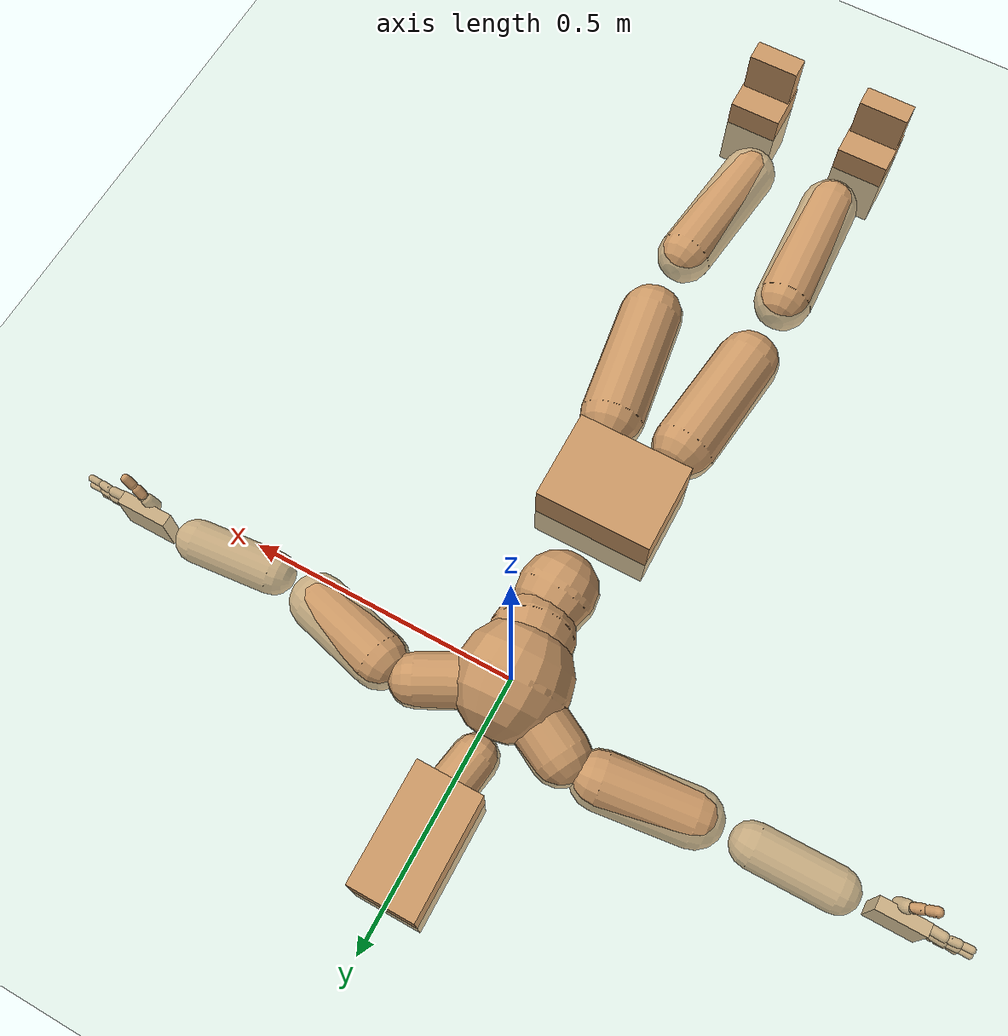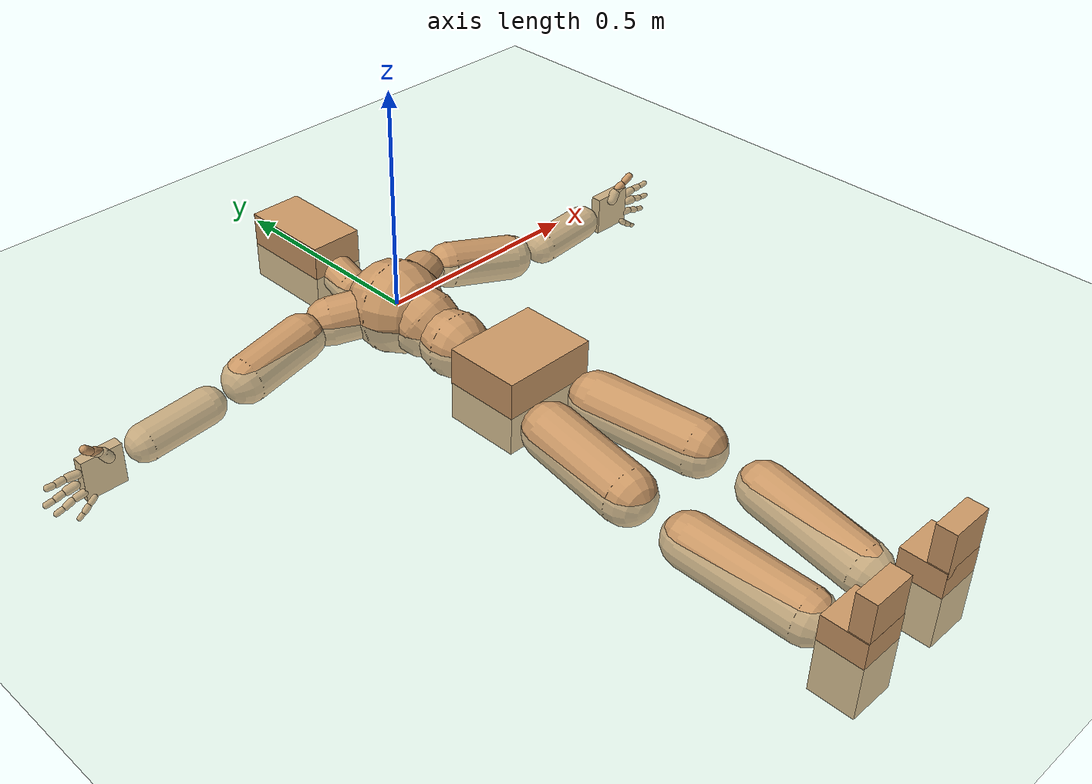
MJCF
<mujoco model="humanoid">
  <compiler coordinate="local"/>
  <default>
    <joint damping="0.0" armature="0.01" stiffness="0.0" limited="true"/>
    <geom conaffinity="1" condim="3" contype="7" margin="0.001" rgba="0.8 0.6 .4 1"/>
  </default>
  <asset>
    <texture type="skybox" builtin="gradient" rgb1=".4 .5 .6" rgb2="0 0 0" width="100" height="100"/>
    <texture builtin="flat" height="1278" mark="cross" markrgb="1 1 1" name="texgeom" random="0.01" rgb1="0.8 0.6 0.4" rgb2="0.8 0.6 0.4" type="cube" width="127"/>
    <texture builtin="checker" height="100" name="texplane" rgb1="0 0 0" rgb2="0.8 0.8 0.8" type="2d" width="100"/>
    <material name="MatPlane" reflectance="0.5" shininess="1" specular="1" texrepeat="60 60" texture="texplane"/>
    <material name="geom" texture="texgeom" texuniform="true"/>
  </asset>
  <worldbody>
    <light cutoff="100" diffuse="1 1 1" dir="-0 0 -1.3" directional="true" exponent="1" pos="0 0 1.3" specular=".1 .1 .1"/>
    <geom conaffinity="1" condim="3" name="floor" pos="0 0 0" rgba="0.8 0.9 0.8 1" size="100 100 .2" type="plane" material="MatPlane"/>

    <body name="Pelvis" mocap="true" pos="0.0031 -0.3514 0.012">
      <geom type="box" pos="-0.0031 -0.0215 -0.0168" size="0.1079 0.0846 0.084" quat="1.0000 0.0000 0.0000 0.0000" density="3021.964159" name="Pelvis"/>
      <body name="L_Hip" pos="0.0582 -0.0928 -0.026">
        <joint name="L_Hip_x" type="hinge" pos="0 0 0" axis="1 0 0" user="250 2.5 1 500 10 2" armature="0.01" range="-180.0000 180.0000" damping="0" stiffness="0"/>
        <joint name="L_Hip_y" type="hinge" pos="0 0 0" axis="0 1 0" user="250 2.5 1 500 10 2" armature="0.01" range="-180.0000 180.0000" damping="0" stiffness="0"/>
        <joint name="L_Hip_z" type="hinge" pos="0 0 0" axis="0 0 1" user="250 2.5 1 500 10 2" armature="0.01" range="-180.0000 180.0000" damping="0" stiffness="0"/>
        <geom type="capsule" contype="1" conaffinity="1" density="2040.816327" fromto="0.0109 -0.0758 -0.0019 0.0438 -0.3030 -0.0075" size="0.0605" name="L_Hip"/>
        <body name="L_Knee" pos="0.0547 -0.3788 -0.0094">
          <joint name="L_Knee_x" type="hinge" pos="0 0 0" axis="1 0 0" user="250 2.5 1 500 10 2" armature="0.01" range="-180.0000 180.0000" damping="0" stiffness="0"/>
          <joint name="L_Knee_y" type="hinge" pos="0 0 0" axis="0 1 0" user="250 2.5 1 500 10 2" armature="0.01" range="-180.0000 180.0000" damping="0" stiffness="0"/>
          <joint name="L_Knee_z" type="hinge" pos="0 0 0" axis="0 0 1" user="250 2.5 1 500 10 2" armature="0.01" range="-180.0000 180.0000" damping="0" stiffness="0"/>
          <geom type="capsule" contype="1" conaffinity="1" density="1234.567901" fromto="-0.0087 -0.0806 -0.0064 -0.0348 -0.3224 -0.0255" size="0.0533" name="L_Knee"/>
          <body name="L_Ankle" pos="-0.0435 -0.4031 -0.0319">
            <joint name="L_Ankle_x" type="hinge" pos="0 0 0" axis="1 0 0" user="150 2.5 1 500 10 2" armature="0.01" range="-180.0000 180.0000" damping="0" stiffness="0"/>
            <joint name="L_Ankle_y" type="hinge" pos="0 0 0" axis="0 1 0" user="150 2.5 1 500 10 2" armature="0.01" range="-180.0000 180.0000" damping="0" stiffness="0"/>
            <joint name="L_Ankle_z" type="hinge" pos="0 0 0" axis="0 0 1" user="150 2.5 1 500 10 2" armature="0.01" range="-180.0000 180.0000" damping="0" stiffness="0"/>
            <geom type="box" pos="0.0407 -0.0287 0.0232" size="0.0498 0.0464 0.0857" quat="1.0000 0.0000 0.0000 0.0000" density="445.819015" name="L_Ankle"/>
            <body name="L_Toe" pos="0.0473 -0.058 0.1182">
              <joint name="L_Toe_x" type="hinge" pos="0 0 0" axis="1 0 0" user="150 1 1 500 1 1" armature="0.01" range="-180.0000 180.0000" damping="0" stiffness="0"/>
              <joint name="L_Toe_y" type="hinge" pos="0 0 0" axis="0 1 0" user="150 1 1 500 1 1" armature="0.01" range="-180.0000 180.0000" damping="0" stiffness="0"/>
              <joint name="L_Toe_z" type="hinge" pos="0 0 0" axis="0 0 1" user="150 1 1 500 1 1" armature="0.01" range="-180.0000 180.0000" damping="0" stiffness="0"/>
              <geom type="box" pos="-0.0065 0.0034 0.0256" size="0.0478 0.0205 0.0495" quat="1.0000 0.0000 0.0000 0.0000" density="421.767577" name="L_Toe"/>
            </body>
          </body>
        </body>
      </body>
      <body name="R_Hip" pos="-0.0633 -0.1039 -0.0213">
        <joint name="R_Hip_x" type="hinge" pos="0 0 0" axis="1 0 0" user="250 2.5 1 500 10 2" armature="0.01" range="-180.0000 180.0000" damping="0" stiffness="0"/>
        <joint name="R_Hip_y" type="hinge" pos="0 0 0" axis="0 1 0" user="250 2.5 1 500 10 2" armature="0.01" range="-180.0000 180.0000" damping="0" stiffness="0"/>
        <joint name="R_Hip_z" type="hinge" pos="0 0 0" axis="0 0 1" user="250 2.5 1 500 10 2" armature="0.01" range="-180.0000 180.0000" damping="0" stiffness="0"/>
        <geom type="capsule" contype="1" conaffinity="1" density="2040.816327" fromto="-0.0088 -0.0725 -0.0034 -0.0354 -0.2899 -0.0135" size="0.0598" name="R_Hip"/>
        <body name="R_Knee" pos="-0.0442 -0.3624 -0.0168">
          <joint name="R_Knee_x" type="hinge" pos="0 0 0" axis="1 0 0" user="250 2.5 1 500 10 2" armature="0.01" range="-180.0000 180.0000" damping="0" stiffness="0"/>
          <joint name="R_Knee_y" type="hinge" pos="0 0 0" axis="0 1 0" user="250 2.5 1 500 10 2" armature="0.01" range="-180.0000 180.0000" damping="0" stiffness="0"/>
          <joint name="R_Knee_z" type="hinge" pos="0 0 0" axis="0 0 1" user="250 2.5 1 500 10 2" armature="0.01" range="-180.0000 180.0000" damping="0" stiffness="0"/>
          <geom type="capsule" contype="1" conaffinity="1" density="1234.567901" fromto="0.0031 -0.0821 -0.0040 0.0123 -0.3286 -0.0162" size="0.0551" name="R_Knee"/>
          <body name="R_Ankle" pos="0.0154 -0.4107 -0.0202">
            <joint name="R_Ankle_x" type="hinge" pos="0 0 0" axis="1 0 0" user="150 1 1 500 10 2" armature="0.01" range="-180.0000 180.0000" damping="0" stiffness="0"/>
            <joint name="R_Ankle_y" type="hinge" pos="0 0 0" axis="0 1 0" user="150 1 1 500 10 2" armature="0.01" range="-180.0000 180.0000" damping="0" stiffness="0"/>
            <joint name="R_Ankle_z" type="hinge" pos="0 0 0" axis="0 0 1" user="150 1 1 500 10 2" armature="0.01" range="-180.0000 180.0000" damping="0" stiffness="0"/>
            <geom type="box" pos="-0.0243 -0.0263 0.0142" size="0.0498 0.0464 0.0857" quat="1.0000 0.0000 0.0000 0.0000" density="445.807856" name="R_Ankle"/>
            <body name="R_Toe" pos="-0.0388 -0.0583 0.119">
              <joint name="R_Toe_x" type="hinge" pos="0 0 0" axis="1 0 0" user="150 1 1 500 1 1" armature="0.01" range="-180.0000 180.0000" damping="0" stiffness="0"/>
              <joint name="R_Toe_y" type="hinge" pos="0 0 0" axis="0 1 0" user="150 1 1 500 1 1" armature="0.01" range="-180.0000 180.0000" damping="0" stiffness="0"/>
              <joint name="R_Toe_z" type="hinge" pos="0 0 0" axis="0 0 1" user="150 1 1 500 1 1" armature="0.01" range="-180.0000 180.0000" damping="0" stiffness="0"/>
              <geom type="box" pos="0.0145 0.0062 0.0158" size="0.0478 0.0205 0.0495" quat="1.0000 0.0000 0.0000 0.0000" density="421.7641" name="R_Toe"/>
            </body>
          </body>
        </body>
      </body>
      <body name="Torso" pos="-0.0028 0.1099 -0.0276">
        <joint name="Torso_x" type="hinge" pos="0 0 0" axis="1 0 0" user="500 5 1 500 10 2" armature="0.01" range="-180.0000 180.0000" damping="0" stiffness="0"/>
        <joint name="Torso_y" type="hinge" pos="0 0 0" axis="0 1 0" user="500 5 1 500 10 2" armature="0.01" range="-180.0000 180.0000" damping="0" stiffness="0"/>
        <joint name="Torso_z" type="hinge" pos="0 0 0" axis="0 0 1" user="500 5 1 500 10 2" armature="0.01" range="-180.0000 180.0000" damping="0" stiffness="0"/>
        <geom type="capsule" contype="1" conaffinity="1" density="2040.816327" fromto="0.0043 0.0593 -0.0027 0.0052 0.0725 -0.0033" size="0.0719" name="Torso"/>
        <body name="Spine" pos="0.0094 0.1319 -0.0059">
          <joint name="Spine_x" type="hinge" pos="0 0 0" axis="1 0 0" user="500 5 1 500 10 2" armature="0.01" range="-180.0000 180.0000" damping="0" stiffness="0"/>
          <joint name="Spine_y" type="hinge" pos="0 0 0" axis="0 1 0" user="500 5 1 500 10 2" armature="0.01" range="-180.0000 180.0000" damping="0" stiffness="0"/>
          <joint name="Spine_z" type="hinge" pos="0 0 0" axis="0 0 1" user="500 5 1 500 10 2" armature="0.01" range="-180.0000 180.0000" damping="0" stiffness="0"/>
          <geom type="capsule" contype="1" conaffinity="1" density="2040.816327" fromto="-0.0051 0.0235 0.0128 -0.0062 0.0287 0.0156" size="0.076" name="Spine"/>
          <body name="Chest" pos="-0.0113 0.0522 0.0284">
            <joint name="Chest_x" type="hinge" pos="0 0 0" axis="1 0 0" user="500 5 1 500 10 2" armature="0.01" range="-180.0000 180.0000" damping="0" stiffness="0"/>
            <joint name="Chest_y" type="hinge" pos="0 0 0" axis="0 1 0" user="500 5 1 500 10 2" armature="0.01" range="-180.0000 180.0000" damping="0" stiffness="0"/>
            <joint name="Chest_z" type="hinge" pos="0 0 0" axis="0 0 1" user="500 5 1 500 10 2" armature="0.01" range="-180.0000 180.0000" damping="0" stiffness="0"/>
            <geom type="capsule" contype="1" conaffinity="1" density="2040.816327" fromto="-0.0020 0.0502 -0.0078 -0.0025 0.0613 -0.0096" size="0.1028" name="Chest"/>
            <body name="Neck" pos="-0.0122 0.1652 -0.0316">
              <joint name="Neck_x" type="hinge" pos="0 0 0" axis="1 0 0" user="150 1 1 250 50 4" armature="0.01" range="-180.0000 180.0000" damping="0" stiffness="0"/>
              <joint name="Neck_y" type="hinge" pos="0 0 0" axis="0 1 0" user="150 1 1 250 50 4" armature="0.01" range="-180.0000 180.0000" damping="0" stiffness="0"/>
              <joint name="Neck_z" type="hinge" pos="0 0 0" axis="0 0 1" user="150 1 1 250 50 4" armature="0.01" range="-180.0000 180.0000" damping="0" stiffness="0"/>
              <geom type="capsule" contype="1" conaffinity="1" density="1000" fromto="0.0050 0.0321 0.0041 0.0198 0.1284 0.0166" size="0.0419" name="Neck"/>
              <body name="Head" pos="0.0248 0.1605 0.0207">
                <joint name="Head_x" type="hinge" pos="0 0 0" axis="1 0 0" user="150 1 1 250 50 4" armature="0.01" range="-180.0000 180.0000" damping="0" stiffness="0"/>
                <joint name="Head_y" type="hinge" pos="0 0 0" axis="0 1 0" user="150 1 1 250 50 4" armature="0.01" range="-180.0000 180.0000" damping="0" stiffness="0"/>
                <joint name="Head_z" type="hinge" pos="0 0 0" axis="0 0 1" user="150 1 1 250 50 4" armature="0.01" range="-180.0000 180.0000" damping="0" stiffness="0"/>
                <geom type="box" pos="-0.0111 0.0414 -0.0008" size="0.0609 0.1096 0.0797" quat="1.0000 0.0000 0.0000 0.0000" density="1018.531753" name="Head"/>
              </body>
            </body>
            <body name="L_Thorax" pos="0.0464 0.0849 -0.0072">
              <joint name="L_Thorax_x" type="hinge" pos="0 0 0" axis="1 0 0" user="200 2 1 500 50 4" armature="0.01" range="-180.0000 180.0000" damping="0" stiffness="0"/>
              <joint name="L_Thorax_y" type="hinge" pos="0 0 0" axis="0 1 0" user="200 2 1 500 50 4" armature="0.01" range="-180.0000 180.0000" damping="0" stiffness="0"/>
              <joint name="L_Thorax_z" type="hinge" pos="0 0 0" axis="0 0 1" user="200 2 1 500 50 4" armature="0.01" range="-180.0000 180.0000" damping="0" stiffness="0"/>
              <geom type="capsule" contype="1" conaffinity="1" density="1000" fromto="0.0238 0.0115 -0.0031 0.0954 0.0462 -0.0124" size="0.0488" name="L_Thorax"/>
              <body name="L_Shoulder" pos="0.1192 0.0577 -0.0155">
                <joint name="L_Shoulder_x" type="hinge" pos="0 0 0" axis="1 0 0" user="200 2 1 500 50 4" armature="0.01" range="-180.0000 180.0000" damping="0" stiffness="0"/>
                <joint name="L_Shoulder_y" type="hinge" pos="0 0 0" axis="0 1 0" user="200 2 1 500 50 4" armature="0.01" range="-180.0000 180.0000" damping="0" stiffness="0"/>
                <joint name="L_Shoulder_z" type="hinge" pos="0 0 0" axis="0 0 1" user="200 2 1 500 50 4" armature="0.01" range="-180.0000 180.0000" damping="0" stiffness="0"/>
                <geom type="capsule" contype="1" conaffinity="1" density="1000" fromto="0.0508 -0.0144 -0.0085 0.2033 -0.0577 -0.0340" size="0.0522" name="L_Shoulder"/>
                <body name="L_Elbow" pos="0.2541 -0.0722 -0.0425">
                  <joint name="L_Elbow_x" type="hinge" pos="0 0 0" axis="1 0 0" user="150 1 1 150 10 2" armature="0.01" range="-720.0000 720.0000" damping="0" stiffness="0"/>
                  <joint name="L_Elbow_y" type="hinge" pos="0 0 0" axis="0 1 0" user="150 1 1 150 10 2" armature="0.01" range="-720.0000 720.0000" damping="0" stiffness="0"/>
                  <joint name="L_Elbow_z" type="hinge" pos="0 0 0" axis="0 0 1" user="150 1 1 150 10 2" armature="0.01" range="-720.0000 720.0000" damping="0" stiffness="0"/>
                  <geom type="capsule" contype="1" conaffinity="1" density="1000" fromto="0.0504 0.0046 -0.0005 0.2016 0.0186 -0.0020" size="0.0401" name="L_Elbow"/>
                  <body name="L_Wrist" pos="0.252 0.0232 -0.0025">
                    <joint name="L_Wrist_x" type="hinge" pos="0 0 0" axis="1 0 0" user="100 1 1 150 1 1" armature="0.01" range="-180.0000 180.0000" damping="0" stiffness="0"/>
                    <joint name="L_Wrist_y" type="hinge" pos="0 0 0" axis="0 1 0" user="100 1 1 150 1 1" armature="0.01" range="-180.0000 180.0000" damping="0" stiffness="0"/>
                    <joint name="L_Wrist_z" type="hinge" pos="0 0 0" axis="0 0 1" user="100 1 1 150 1 1" armature="0.01" range="-180.0000 180.0000" damping="0" stiffness="0"/>
                    <geom type="box" pos="0.0523 -0.0013 -0.0031" size="0.0484 0.0122 0.046" quat="1.0000 0.0000 0.0000 0.0000" density="1198.335963" name="L_Wrist"/>
                    <body name="L_Index1" pos="0.1019 -0.0087 0.0194">
                      <joint name="L_Index1_x" type="hinge" pos="0 0 0" axis="1 0 0" user="100 10 1 150" armature="0.01" range="-180.0000 180.0000" damping="0" stiffness="0"/>
                      <joint name="L_Index1_y" type="hinge" pos="0 0 0" axis="0 1 0" user="100 10 1 150" armature="0.01" range="-180.0000 180.0000" damping="0" stiffness="0"/>
                      <joint name="L_Index1_z" type="hinge" pos="0 0 0" axis="0 0 1" user="100 10 1 150" armature="0.01" range="-180.0000 180.0000" damping="0" stiffness="0"/>
                      <geom type="capsule" contype="1" conaffinity="1" density="1000" fromto="0.0064 0.0004 0.0006 0.0256 0.0018 0.0024" size="0.0091" name="L_Index1"/>
                      <body name="L_Index2" pos="0.0319 0.0022 0.003">
                        <joint name="L_Index2_x" type="hinge" pos="0 0 0" axis="1 0 0" user="100 10 1 150" armature="0.01" range="-180.0000 180.0000" damping="0" stiffness="0"/>
                        <joint name="L_Index2_y" type="hinge" pos="0 0 0" axis="0 1 0" user="100 10 1 150" armature="0.01" range="-180.0000 180.0000" damping="0" stiffness="0"/>
                        <joint name="L_Index2_z" type="hinge" pos="0 0 0" axis="0 0 1" user="100 10 1 150" armature="0.01" range="-180.0000 180.0000" damping="0" stiffness="0"/>
                        <geom type="capsule" contype="1" conaffinity="1" density="1000" fromto="0.0045 -0.0005 0.0000 0.0180 -0.0019 0.0000" size="0.0076" name="L_Index2"/>
                        <body name="L_Index3" pos="0.0225 -0.0024 0.0001">
                          <joint name="L_Index3_x" type="hinge" pos="0 0 0" axis="1 0 0" user="100 10 1 150" armature="0.01" range="-180.0000 180.0000" damping="0" stiffness="0"/>
                          <joint name="L_Index3_y" type="hinge" pos="0 0 0" axis="0 1 0" user="100 10 1 150" armature="0.01" range="-180.0000 180.0000" damping="0" stiffness="0"/>
                          <joint name="L_Index3_z" type="hinge" pos="0 0 0" axis="0 0 1" user="100 10 1 150" armature="0.01" range="-180.0000 180.0000" damping="0" stiffness="0"/>
                          <geom type="capsule" contype="1" conaffinity="1" density="1000" fromto="0.0049 -0.0001 0.0004 0.0196 -0.0003 0.0016" size="0.0064" name="L_Index3"/>
                        </body>
                      </body>
                    </body>
                    <body name="L_Middle1" pos="0.1094 -0.0063 -0.004">
                      <joint name="L_Middle1_x" type="hinge" pos="0 0 0" axis="1 0 0" user="100 10 1 150" armature="0.01" range="-180.0000 180.0000" damping="0" stiffness="0"/>
                      <joint name="L_Middle1_y" type="hinge" pos="0 0 0" axis="0 1 0" user="100 10 1 150" armature="0.01" range="-180.0000 180.0000" damping="0" stiffness="0"/>
                      <joint name="L_Middle1_z" type="hinge" pos="0 0 0" axis="0 0 1" user="100 10 1 150" armature="0.01" range="-180.0000 180.0000" damping="0" stiffness="0"/>
                      <geom type="capsule" contype="1" conaffinity="1" density="1000" fromto="0.0061 0.0002 -0.0008 0.0245 0.0006 -0.0032" size="0.0094" name="L_Middle1"/>
                      <body name="L_Middle2" pos="0.0306 0.0008 -0.004">
                        <joint name="L_Middle2_x" type="hinge" pos="0 0 0" axis="1 0 0" user="100 10 1 150" armature="0.01" range="-180.0000 180.0000" damping="0" stiffness="0"/>
                        <joint name="L_Middle2_y" type="hinge" pos="0 0 0" axis="0 1 0" user="100 10 1 150" armature="0.01" range="-180.0000 180.0000" damping="0" stiffness="0"/>
                        <joint name="L_Middle2_z" type="hinge" pos="0 0 0" axis="0 0 1" user="100 10 1 150" armature="0.01" range="-180.0000 180.0000" damping="0" stiffness="0"/>
                        <geom type="capsule" contype="1" conaffinity="1" density="1000" fromto="0.0047 -0.0004 -0.0008 0.0188 -0.0016 -0.0033" size="0.007" name="L_Middle2"/>
                        <body name="L_Middle3" pos="0.0235 -0.002 -0.0041">
                          <joint name="L_Middle3_x" type="hinge" pos="0 0 0" axis="1 0 0" user="100 10 1 150" armature="0.01" range="-180.0000 180.0000" damping="0" stiffness="0"/>
                          <joint name="L_Middle3_y" type="hinge" pos="0 0 0" axis="0 1 0" user="100 10 1 150" armature="0.01" range="-180.0000 180.0000" damping="0" stiffness="0"/>
                          <joint name="L_Middle3_z" type="hinge" pos="0 0 0" axis="0 0 1" user="100 10 1 150" armature="0.01" range="-180.0000 180.0000" damping="0" stiffness="0"/>
                          <geom type="capsule" contype="1" conaffinity="1" density="1000" fromto="0.0051 -0.0000 -0.0004 0.0204 -0.0000 -0.0017" size="0.0061" name="L_Middle3"/>
                        </body>
                      </body>
                    </body>
                    <body name="L_Pinky1" pos="0.084 -0.0145 -0.0437">
                      <joint name="L_Pinky1_x" type="hinge" pos="0 0 0" axis="1 0 0" user="100 10 1 150" armature="0.01" range="-180.0000 180.0000" damping="0" stiffness="0"/>
                      <joint name="L_Pinky1_y" type="hinge" pos="0 0 0" axis="0 1 0" user="100 10 1 150" armature="0.01" range="-180.0000 180.0000" damping="0" stiffness="0"/>
                      <joint name="L_Pinky1_z" type="hinge" pos="0 0 0" axis="0 0 1" user="100 10 1 150" armature="0.01" range="-180.0000 180.0000" damping="0" stiffness="0"/>
                      <geom type="capsule" contype="1" conaffinity="1" density="1000" fromto="0.0031 -0.0002 -0.0024 0.0124 -0.0009 -0.0096" size="0.0067" name="L_Pinky1"/>
                      <body name="L_Pinky2" pos="0.0155 -0.0011 -0.012">
                        <joint name="L_Pinky2_x" type="hinge" pos="0 0 0" axis="1 0 0" user="100 10 1 150" armature="0.01" range="-180.0000 180.0000" damping="0" stiffness="0"/>
                        <joint name="L_Pinky2_y" type="hinge" pos="0 0 0" axis="0 1 0" user="100 10 1 150" armature="0.01" range="-180.0000 180.0000" damping="0" stiffness="0"/>
                        <joint name="L_Pinky2_z" type="hinge" pos="0 0 0" axis="0 0 1" user="100 10 1 150" armature="0.01" range="-180.0000 180.0000" damping="0" stiffness="0"/>
                        <geom type="capsule" contype="1" conaffinity="1" density="1000" fromto="0.0031 -0.0003 -0.0022 0.0124 -0.0013 -0.0090" size="0.0065" name="L_Pinky2"/>
                        <body name="L_Pinky3" pos="0.0155 -0.0017 -0.0112">
                          <joint name="L_Pinky3_x" type="hinge" pos="0 0 0" axis="1 0 0" user="100 10 1 150" armature="0.01" range="-180.0000 180.0000" damping="0" stiffness="0"/>
                          <joint name="L_Pinky3_y" type="hinge" pos="0 0 0" axis="0 1 0" user="100 10 1 150" armature="0.01" range="-180.0000 180.0000" damping="0" stiffness="0"/>
                          <joint name="L_Pinky3_z" type="hinge" pos="0 0 0" axis="0 0 1" user="100 10 1 150" armature="0.01" range="-180.0000 180.0000" damping="0" stiffness="0"/>
                          <geom type="capsule" contype="1" conaffinity="1" density="1000" fromto="0.0035 0.0001 -0.0018 0.0140 0.0003 -0.0074" size="0.005" name="L_Pinky3"/>
                        </body>
                      </body>
                    </body>
                    <body name="L_Ring1" pos="0.0974 -0.0093 -0.0273">
                      <joint name="L_Ring1_x" type="hinge" pos="0 0 0" axis="1 0 0" user="100 10 1 150" armature="0.01" range="-180.0000 180.0000" damping="0" stiffness="0"/>
                      <joint name="L_Ring1_y" type="hinge" pos="0 0 0" axis="0 1 0" user="100 10 1 150" armature="0.01" range="-180.0000 180.0000" damping="0" stiffness="0"/>
                      <joint name="L_Ring1_z" type="hinge" pos="0 0 0" axis="0 0 1" user="100 10 1 150" armature="0.01" range="-180.0000 180.0000" damping="0" stiffness="0"/>
                      <geom type="capsule" contype="1" conaffinity="1" density="1000" fromto="0.0056 0.0003 -0.0011 0.0224 0.0012 -0.0042" size="0.008" name="L_Ring1"/>
                      <body name="L_Ring2" pos="0.028 0.0015 -0.0053">
                        <joint name="L_Ring2_x" type="hinge" pos="0 0 0" axis="1 0 0" user="100 10 1 150" armature="0.01" range="-180.0000 180.0000" damping="0" stiffness="0"/>
                        <joint name="L_Ring2_y" type="hinge" pos="0 0 0" axis="0 1 0" user="100 10 1 150" armature="0.01" range="-180.0000 180.0000" damping="0" stiffness="0"/>
                        <joint name="L_Ring2_z" type="hinge" pos="0 0 0" axis="0 0 1" user="100 10 1 150" armature="0.01" range="-180.0000 180.0000" damping="0" stiffness="0"/>
                        <geom type="capsule" contype="1" conaffinity="1" density="1000" fromto="0.0046 -0.0003 -0.0014 0.0183 -0.0012 -0.0057" size="0.0074" name="L_Ring2"/>
                        <body name="L_Ring3" pos="0.0228 -0.0015 -0.0071">
                          <joint name="L_Ring3_x" type="hinge" pos="0 0 0" axis="1 0 0" user="100 10 1 150" armature="0.01" range="-180.0000 180.0000" damping="0" stiffness="0"/>
                          <joint name="L_Ring3_y" type="hinge" pos="0 0 0" axis="0 1 0" user="100 10 1 150" armature="0.01" range="-180.0000 180.0000" damping="0" stiffness="0"/>
                          <joint name="L_Ring3_z" type="hinge" pos="0 0 0" axis="0 0 1" user="100 10 1 150" armature="0.01" range="-180.0000 180.0000" damping="0" stiffness="0"/>
                          <geom type="capsule" contype="1" conaffinity="1" density="1000" fromto="0.0050 0.0001 -0.0010 0.0199 0.0004 -0.0041" size="0.0057" name="L_Ring3"/>
                        </body>
                      </body>
                    </body>
                    <body name="L_Thumb1" pos="0.0406 -0.018 0.0256">
                      <joint name="L_Thumb1_x" type="hinge" pos="0 0 0" axis="1 0 0" user="100 10 1 150" armature="0.01" range="-180.0000 180.0000" damping="0" stiffness="0"/>
                      <joint name="L_Thumb1_y" type="hinge" pos="0 0 0" axis="0 1 0" user="100 10 1 150" armature="0.01" range="-180.0000 180.0000" damping="0" stiffness="0"/>
                      <joint name="L_Thumb1_z" type="hinge" pos="0 0 0" axis="0 0 1" user="100 10 1 150" armature="0.01" range="-180.0000 180.0000" damping="0" stiffness="0"/>
                      <geom type="capsule" contype="1" conaffinity="1" density="1000" fromto="0.0034 0.0002 0.0050 0.0136 0.0008 0.0200" size="0.012" name="L_Thumb1"/>
                      <body name="L_Thumb2" pos="0.017 0.001 0.025">
                        <joint name="L_Thumb2_x" type="hinge" pos="0 0 0" axis="1 0 0" user="100 10 1 150" armature="0.01" range="-180.0000 180.0000" damping="0" stiffness="0"/>
                        <joint name="L_Thumb2_y" type="hinge" pos="0 0 0" axis="0 1 0" user="100 10 1 150" armature="0.01" range="-180.0000 180.0000" damping="0" stiffness="0"/>
                        <joint name="L_Thumb2_z" type="hinge" pos="0 0 0" axis="0 0 1" user="100 10 1 150" armature="0.01" range="-180.0000 180.0000" damping="0" stiffness="0"/>
                        <geom type="capsule" contype="1" conaffinity="1" density="1000" fromto="0.0041 -0.0010 0.0031 0.0164 -0.0041 0.0124" size="0.0095" name="L_Thumb2"/>
                        <body name="L_Thumb3" pos="0.0205 -0.0052 0.0155">
                          <joint name="L_Thumb3_x" type="hinge" pos="0 0 0" axis="1 0 0" user="100 10 1 150" armature="0.01" range="-180.0000 180.0000" damping="0" stiffness="0"/>
                          <joint name="L_Thumb3_y" type="hinge" pos="0 0 0" axis="0 1 0" user="100 10 1 150" armature="0.01" range="-180.0000 180.0000" damping="0" stiffness="0"/>
                          <joint name="L_Thumb3_z" type="hinge" pos="0 0 0" axis="0 0 1" user="100 10 1 150" armature="0.01" range="-180.0000 180.0000" damping="0" stiffness="0"/>
                          <geom type="capsule" contype="1" conaffinity="1" density="1000" fromto="0.0045 -0.0006 0.0035 0.0180 -0.0025 0.0140" size="0.0087" name="L_Thumb3"/>
                        </body>
                      </body>
                    </body>
                  </body>
                </body>
              </body>
            </body>
            <body name="R_Thorax" pos="-0.0477 0.0843 -0.0134">
              <joint name="R_Thorax_x" type="hinge" pos="0 0 0" axis="1 0 0" user="200 2 1 150 10 2" armature="0.01" range="-180.0000 180.0000" damping="0" stiffness="0"/>
              <joint name="R_Thorax_y" type="hinge" pos="0 0 0" axis="0 1 0" user="200 2 1 150 10 2" armature="0.01" range="-180.0000 180.0000" damping="0" stiffness="0"/>
              <joint name="R_Thorax_z" type="hinge" pos="0 0 0" axis="0 0 1" user="200 2 1 150 10 2" armature="0.01" range="-180.0000 180.0000" damping="0" stiffness="0"/>
              <geom type="capsule" contype="1" conaffinity="1" density="1000" fromto="-0.0205 0.0107 -0.0025 -0.0821 0.0428 -0.0101" size="0.0536" name="R_Thorax"/>
              <body name="R_Shoulder" pos="-0.1026 0.0535 -0.0127">
                <joint name="R_Shoulder_x" type="hinge" pos="0 0 0" axis="1 0 0" user="200 2 1 250 10 2" armature="0.01" range="-180.0000 180.0000" damping="0" stiffness="0"/>
                <joint name="R_Shoulder_y" type="hinge" pos="0 0 0" axis="0 1 0" user="200 2 1 250 10 2" armature="0.01" range="-180.0000 180.0000" damping="0" stiffness="0"/>
                <joint name="R_Shoulder_z" type="hinge" pos="0 0 0" axis="0 0 1" user="200 2 1 250 10 2" armature="0.01" range="-180.0000 180.0000" damping="0" stiffness="0"/>
                <geom type="capsule" contype="1" conaffinity="1" density="1000" fromto="-0.0542 -0.0073 -0.0053 -0.2169 -0.0292 -0.0212" size="0.0521" name="R_Shoulder"/>
                <body name="R_Elbow" pos="-0.2711 -0.0365 -0.0265">
                  <joint name="R_Elbow_x" type="hinge" pos="0 0 0" axis="1 0 0" user="150 1 1 150 10 2" armature="0.01" range="-720.0000 720.0000" damping="0" stiffness="0"/>
                  <joint name="R_Elbow_y" type="hinge" pos="0 0 0" axis="0 1 0" user="150 1 1 150 10 2" armature="0.01" range="-720.0000 720.0000" damping="0" stiffness="0"/>
                  <joint name="R_Elbow_z" type="hinge" pos="0 0 0" axis="0 0 1" user="150 1 1 150 10 2" armature="0.01" range="-720.0000 720.0000" damping="0" stiffness="0"/>
                  <geom type="capsule" contype="1" conaffinity="1" density="1000" fromto="-0.0499 -0.0009 -0.0031 -0.1994 -0.0036 -0.0123" size="0.0404" name="R_Elbow"/>
                  <body name="R_Wrist" pos="-0.2493 -0.0045 -0.0153">
                    <joint name="R_Wrist_x" type="hinge" pos="0 0 0" axis="1 0 0" user="100 1 1 150 1 1" armature="0.01" range="-180.0000 180.0000" damping="0" stiffness="0"/>
                    <joint name="R_Wrist_y" type="hinge" pos="0 0 0" axis="0 1 0" user="100 1 1 150 1 1" armature="0.01" range="-180.0000 180.0000" damping="0" stiffness="0"/>
                    <joint name="R_Wrist_z" type="hinge" pos="0 0 0" axis="0 0 1" user="100 1 1 150 1 1" armature="0.01" range="-180.0000 180.0000" damping="0" stiffness="0"/>
                    <geom type="box" pos="-0.0537 -0.0044 -0.0029" size="0.0454 0.0122 0.046" quat="1.0000 0.0000 0.0000 0.0000" density="1230.822844" name="R_Wrist"/>
                    <body name="R_Index1" pos="-0.0999 -0.0118 0.0196">
                      <joint name="R_Index1_x" type="hinge" pos="0 0 0" axis="1 0 0" user="100 10 1 150" armature="0.01" range="-180.0000 180.0000" damping="0" stiffness="0"/>
                      <joint name="R_Index1_y" type="hinge" pos="0 0 0" axis="0 1 0" user="100 10 1 150" armature="0.01" range="-180.0000 180.0000" damping="0" stiffness="0"/>
                      <joint name="R_Index1_z" type="hinge" pos="0 0 0" axis="0 0 1" user="100 10 1 150" armature="0.01" range="-180.0000 180.0000" damping="0" stiffness="0"/>
                      <geom type="capsule" contype="1" conaffinity="1" density="1000" fromto="-0.0064 0.0004 0.0006 -0.0256 0.0018 0.0024" size="0.0091" name="R_Index1"/>
                      <body name="R_Index2" pos="-0.0319 0.0022 0.003">
                        <joint name="R_Index2_x" type="hinge" pos="0 0 0" axis="1 0 0" user="100 10 1 150" armature="0.01" range="-180.0000 180.0000" damping="0" stiffness="0"/>
                        <joint name="R_Index2_y" type="hinge" pos="0 0 0" axis="0 1 0" user="100 10 1 150" armature="0.01" range="-180.0000 180.0000" damping="0" stiffness="0"/>
                        <joint name="R_Index2_z" type="hinge" pos="0 0 0" axis="0 0 1" user="100 10 1 150" armature="0.01" range="-180.0000 180.0000" damping="0" stiffness="0"/>
                        <geom type="capsule" contype="1" conaffinity="1" density="1000" fromto="-0.0045 -0.0005 0.0000 -0.0180 -0.0019 0.0000" size="0.0076" name="R_Index2"/>
                        <body name="R_Index3" pos="-0.0225 -0.0023 0.0001">
                          <joint name="R_Index3_x" type="hinge" pos="0 0 0" axis="1 0 0" user="100 10 1 150" armature="0.01" range="-180.0000 180.0000" damping="0" stiffness="0"/>
                          <joint name="R_Index3_y" type="hinge" pos="0 0 0" axis="0 1 0" user="100 10 1 150" armature="0.01" range="-180.0000 180.0000" damping="0" stiffness="0"/>
                          <joint name="R_Index3_z" type="hinge" pos="0 0 0" axis="0 0 1" user="100 10 1 150" armature="0.01" range="-180.0000 180.0000" damping="0" stiffness="0"/>
                          <geom type="capsule" contype="1" conaffinity="1" density="1000" fromto="-0.0041 -0.0001 0.0004 -0.0164 -0.0003 0.0016" size="0.0067" name="R_Index3"/>
                        </body>
                      </body>
                    </body>
                    <body name="R_Middle1" pos="-0.1074 -0.0094 -0.0037">
                      <joint name="R_Middle1_x" type="hinge" pos="0 0 0" axis="1 0 0" user="100 10 1 150" armature="0.01" range="-180.0000 180.0000" damping="0" stiffness="0"/>
                      <joint name="R_Middle1_y" type="hinge" pos="0 0 0" axis="0 1 0" user="100 10 1 150" armature="0.01" range="-180.0000 180.0000" damping="0" stiffness="0"/>
                      <joint name="R_Middle1_z" type="hinge" pos="0 0 0" axis="0 0 1" user="100 10 1 150" armature="0.01" range="-180.0000 180.0000" damping="0" stiffness="0"/>
                      <geom type="capsule" contype="1" conaffinity="1" density="1000" fromto="-0.0061 0.0002 -0.0008 -0.0245 0.0006 -0.0032" size="0.0094" name="R_Middle1"/>
                      <body name="R_Middle2" pos="-0.0306 0.0008 -0.004">
                        <joint name="R_Middle2_x" type="hinge" pos="0 0 0" axis="1 0 0" user="100 10 1 150" armature="0.01" range="-180.0000 180.0000" damping="0" stiffness="0"/>
                        <joint name="R_Middle2_y" type="hinge" pos="0 0 0" axis="0 1 0" user="100 10 1 150" armature="0.01" range="-180.0000 180.0000" damping="0" stiffness="0"/>
                        <joint name="R_Middle2_z" type="hinge" pos="0 0 0" axis="0 0 1" user="100 10 1 150" armature="0.01" range="-180.0000 180.0000" damping="0" stiffness="0"/>
                        <geom type="capsule" contype="1" conaffinity="1" density="1000" fromto="-0.0047 -0.0004 -0.0008 -0.0188 -0.0016 -0.0033" size="0.007" name="R_Middle2"/>
                        <body name="R_Middle3" pos="-0.0235 -0.002 -0.0041">
                          <joint name="R_Middle3_x" type="hinge" pos="0 0 0" axis="1 0 0" user="100 10 1 150" armature="0.01" range="-180.0000 180.0000" damping="0" stiffness="0"/>
                          <joint name="R_Middle3_y" type="hinge" pos="0 0 0" axis="0 1 0" user="100 10 1 150" armature="0.01" range="-180.0000 180.0000" damping="0" stiffness="0"/>
                          <joint name="R_Middle3_z" type="hinge" pos="0 0 0" axis="0 0 1" user="100 10 1 150" armature="0.01" range="-180.0000 180.0000" damping="0" stiffness="0"/>
                          <geom type="capsule" contype="1" conaffinity="1" density="1000" fromto="-0.0043 -0.0000 -0.0004 -0.0172 -0.0000 -0.0017" size="0.0064" name="R_Middle3"/>
                        </body>
                      </body>
                    </body>
                    <body name="R_Pinky1" pos="-0.082 -0.0176 -0.0435">
                      <joint name="R_Pinky1_x" type="hinge" pos="0 0 0" axis="1 0 0" user="100 10 1 150" armature="0.01" range="-180.0000 180.0000" damping="0" stiffness="0"/>
                      <joint name="R_Pinky1_y" type="hinge" pos="0 0 0" axis="0 1 0" user="100 10 1 150" armature="0.01" range="-180.0000 180.0000" damping="0" stiffness="0"/>
                      <joint name="R_Pinky1_z" type="hinge" pos="0 0 0" axis="0 0 1" user="100 10 1 150" armature="0.01" range="-180.0000 180.0000" damping="0" stiffness="0"/>
                      <geom type="capsule" contype="1" conaffinity="1" density="1000" fromto="-0.0031 -0.0002 -0.0024 -0.0124 -0.0009 -0.0096" size="0.0067" name="R_Pinky1"/>
                      <body name="R_Pinky2" pos="-0.0155 -0.0011 -0.012">
                        <joint name="R_Pinky2_x" type="hinge" pos="0 0 0" axis="1 0 0" user="100 10 1 150" armature="0.01" range="-180.0000 180.0000" damping="0" stiffness="0"/>
                        <joint name="R_Pinky2_y" type="hinge" pos="0 0 0" axis="0 1 0" user="100 10 1 150" armature="0.01" range="-180.0000 180.0000" damping="0" stiffness="0"/>
                        <joint name="R_Pinky2_z" type="hinge" pos="0 0 0" axis="0 0 1" user="100 10 1 150" armature="0.01" range="-180.0000 180.0000" damping="0" stiffness="0"/>
                        <geom type="capsule" contype="1" conaffinity="1" density="1000" fromto="-0.0031 -0.0003 -0.0022 -0.0124 -0.0013 -0.0090" size="0.0065" name="R_Pinky2"/>
                        <body name="R_Pinky3" pos="-0.0155 -0.0017 -0.0112">
                          <joint name="R_Pinky3_x" type="hinge" pos="0 0 0" axis="1 0 0" user="100 10 1 150" armature="0.01" range="-180.0000 180.0000" damping="0" stiffness="0"/>
                          <joint name="R_Pinky3_y" type="hinge" pos="0 0 0" axis="0 1 0" user="100 10 1 150" armature="0.01" range="-180.0000 180.0000" damping="0" stiffness="0"/>
                          <joint name="R_Pinky3_z" type="hinge" pos="0 0 0" axis="0 0 1" user="100 10 1 150" armature="0.01" range="-180.0000 180.0000" damping="0" stiffness="0"/>
                          <geom type="capsule" contype="1" conaffinity="1" density="1000" fromto="-0.0027 0.0001 -0.0018 -0.0108 0.0003 -0.0074" size="0.0052" name="R_Pinky3"/>
                        </body>
                      </body>
                    </body>
                    <body name="R_Ring1" pos="-0.0954 -0.0124 -0.0271">
                      <joint name="R_Ring1_x" type="hinge" pos="0 0 0" axis="1 0 0" user="100 10 1 150" armature="0.01" range="-180.0000 180.0000" damping="0" stiffness="0"/>
                      <joint name="R_Ring1_y" type="hinge" pos="0 0 0" axis="0 1 0" user="100 10 1 150" armature="0.01" range="-180.0000 180.0000" damping="0" stiffness="0"/>
                      <joint name="R_Ring1_z" type="hinge" pos="0 0 0" axis="0 0 1" user="100 10 1 150" armature="0.01" range="-180.0000 180.0000" damping="0" stiffness="0"/>
                      <geom type="capsule" contype="1" conaffinity="1" density="1000" fromto="-0.0056 0.0003 -0.0011 -0.0224 0.0012 -0.0042" size="0.008" name="R_Ring1"/>
                      <body name="R_Ring2" pos="-0.028 0.0015 -0.0053">
                        <joint name="R_Ring2_x" type="hinge" pos="0 0 0" axis="1 0 0" user="100 10 1 150" armature="0.01" range="-180.0000 180.0000" damping="0" stiffness="0"/>
                        <joint name="R_Ring2_y" type="hinge" pos="0 0 0" axis="0 1 0" user="100 10 1 150" armature="0.01" range="-180.0000 180.0000" damping="0" stiffness="0"/>
                        <joint name="R_Ring2_z" type="hinge" pos="0 0 0" axis="0 0 1" user="100 10 1 150" armature="0.01" range="-180.0000 180.0000" damping="0" stiffness="0"/>
                        <geom type="capsule" contype="1" conaffinity="1" density="1000" fromto="-0.0046 -0.0003 -0.0014 -0.0183 -0.0012 -0.0057" size="0.0074" name="R_Ring2"/>
                        <body name="R_Ring3" pos="-0.0228 -0.0015 -0.0071">
                          <joint name="R_Ring3_x" type="hinge" pos="0 0 0" axis="1 0 0" user="100 10 1 150" armature="0.01" range="-180.0000 180.0000" damping="0" stiffness="0"/>
                          <joint name="R_Ring3_y" type="hinge" pos="0 0 0" axis="0 1 0" user="100 10 1 150" armature="0.01" range="-180.0000 180.0000" damping="0" stiffness="0"/>
                          <joint name="R_Ring3_z" type="hinge" pos="0 0 0" axis="0 0 1" user="100 10 1 150" armature="0.01" range="-180.0000 180.0000" damping="0" stiffness="0"/>
                          <geom type="capsule" contype="1" conaffinity="1" density="1000" fromto="-0.0042 0.0001 -0.0010 -0.0167 0.0004 -0.0041" size="0.006" name="R_Ring3"/>
                        </body>
                      </body>
                    </body>
                    <body name="R_Thumb1" pos="-0.0386 -0.0211 0.0259">
                      <joint name="R_Thumb1_x" type="hinge" pos="0 0 0" axis="1 0 0" user="100 10 1 150" armature="0.01" range="-180.0000 180.0000" damping="0" stiffness="0"/>
                      <joint name="R_Thumb1_y" type="hinge" pos="0 0 0" axis="0 1 0" user="100 10 1 150" armature="0.01" range="-180.0000 180.0000" damping="0" stiffness="0"/>
                      <joint name="R_Thumb1_z" type="hinge" pos="0 0 0" axis="0 0 1" user="100 10 1 150" armature="0.01" range="-180.0000 180.0000" damping="0" stiffness="0"/>
                      <geom type="capsule" contype="1" conaffinity="1" density="1000" fromto="-0.0034 0.0002 0.0050 -0.0136 0.0008 0.0200" size="0.012" name="R_Thumb1"/>
                      <body name="R_Thumb2" pos="-0.017 0.001 0.025">
                        <joint name="R_Thumb2_x" type="hinge" pos="0 0 0" axis="1 0 0" user="100 10 1 150" armature="0.01" range="-180.0000 180.0000" damping="0" stiffness="0"/>
                        <joint name="R_Thumb2_y" type="hinge" pos="0 0 0" axis="0 1 0" user="100 10 1 150" armature="0.01" range="-180.0000 180.0000" damping="0" stiffness="0"/>
                        <joint name="R_Thumb2_z" type="hinge" pos="0 0 0" axis="0 0 1" user="100 10 1 150" armature="0.01" range="-180.0000 180.0000" damping="0" stiffness="0"/>
                        <geom type="capsule" contype="1" conaffinity="1" density="1000" fromto="-0.0041 -0.0010 0.0031 -0.0164 -0.0041 0.0124" size="0.0095" name="R_Thumb2"/>
                        <body name="R_Thumb3" pos="-0.0205 -0.0052 0.0155">
                          <joint name="R_Thumb3_x" type="hinge" pos="0 0 0" axis="1 0 0" user="100 10 1 150" armature="0.01" range="-180.0000 180.0000" damping="0" stiffness="0"/>
                          <joint name="R_Thumb3_y" type="hinge" pos="0 0 0" axis="0 1 0" user="100 10 1 150" armature="0.01" range="-180.0000 180.0000" damping="0" stiffness="0"/>
                          <joint name="R_Thumb3_z" type="hinge" pos="0 0 0" axis="0 0 1" user="100 10 1 150" armature="0.01" range="-180.0000 180.0000" damping="0" stiffness="0"/>
                          <geom type="capsule" contype="1" conaffinity="1" density="1000" fromto="-0.0037 -0.0006 0.0035 -0.0148 -0.0025 0.0140" size="0.009" name="R_Thumb3"/>
                        </body>
                      </body>
                    </body>
                  </body>
                </body>
              </body>
            </body>
          </body>
        </body>
      </body>
    </body>
  </worldbody>
  <actuator>
    <motor name="L_Hip_x" joint="L_Hip_x" gear="1"/>
    <motor name="L_Hip_y" joint="L_Hip_y" gear="1"/>
    <motor name="L_Hip_z" joint="L_Hip_z" gear="1"/>
    <motor name="L_Knee_x" joint="L_Knee_x" gear="1"/>
    <motor name="L_Knee_y" joint="L_Knee_y" gear="1"/>
    <motor name="L_Knee_z" joint="L_Knee_z" gear="1"/>
    <motor name="L_Ankle_x" joint="L_Ankle_x" gear="1"/>
    <motor name="L_Ankle_y" joint="L_Ankle_y" gear="1"/>
    <motor name="L_Ankle_z" joint="L_Ankle_z" gear="1"/>
    <motor name="L_Toe_x" joint="L_Toe_x" gear="1"/>
    <motor name="L_Toe_y" joint="L_Toe_y" gear="1"/>
    <motor name="L_Toe_z" joint="L_Toe_z" gear="1"/>
    <motor name="R_Hip_x" joint="R_Hip_x" gear="1"/>
    <motor name="R_Hip_y" joint="R_Hip_y" gear="1"/>
    <motor name="R_Hip_z" joint="R_Hip_z" gear="1"/>
    <motor name="R_Knee_x" joint="R_Knee_x" gear="1"/>
    <motor name="R_Knee_y" joint="R_Knee_y" gear="1"/>
    <motor name="R_Knee_z" joint="R_Knee_z" gear="1"/>
    <motor name="R_Ankle_x" joint="R_Ankle_x" gear="1"/>
    <motor name="R_Ankle_y" joint="R_Ankle_y" gear="1"/>
    <motor name="R_Ankle_z" joint="R_Ankle_z" gear="1"/>
    <motor name="R_Toe_x" joint="R_Toe_x" gear="1"/>
    <motor name="R_Toe_y" joint="R_Toe_y" gear="1"/>
    <motor name="R_Toe_z" joint="R_Toe_z" gear="1"/>
    <motor name="Torso_x" joint="Torso_x" gear="1"/>
    <motor name="Torso_y" joint="Torso_y" gear="1"/>
    <motor name="Torso_z" joint="Torso_z" gear="1"/>
    <motor name="Spine_x" joint="Spine_x" gear="1"/>
    <motor name="Spine_y" joint="Spine_y" gear="1"/>
    <motor name="Spine_z" joint="Spine_z" gear="1"/>
    <motor name="Chest_x" joint="Chest_x" gear="1"/>
    <motor name="Chest_y" joint="Chest_y" gear="1"/>
    <motor name="Chest_z" joint="Chest_z" gear="1"/>
    <motor name="Neck_x" joint="Neck_x" gear="1"/>
    <motor name="Neck_y" joint="Neck_y" gear="1"/>
    <motor name="Neck_z" joint="Neck_z" gear="1"/>
    <motor name="Head_x" joint="Head_x" gear="1"/>
    <motor name="Head_y" joint="Head_y" gear="1"/>
    <motor name="Head_z" joint="Head_z" gear="1"/>
    <motor name="L_Thorax_x" joint="L_Thorax_x" gear="1"/>
    <motor name="L_Thorax_y" joint="L_Thorax_y" gear="1"/>
    <motor name="L_Thorax_z" joint="L_Thorax_z" gear="1"/>
    <motor name="L_Shoulder_x" joint="L_Shoulder_x" gear="1"/>
    <motor name="L_Shoulder_y" joint="L_Shoulder_y" gear="1"/>
    <motor name="L_Shoulder_z" joint="L_Shoulder_z" gear="1"/>
    <motor name="L_Elbow_x" joint="L_Elbow_x" gear="1"/>
    <motor name="L_Elbow_y" joint="L_Elbow_y" gear="1"/>
    <motor name="L_Elbow_z" joint="L_Elbow_z" gear="1"/>
    <motor name="L_Wrist_x" joint="L_Wrist_x" gear="1"/>
    <motor name="L_Wrist_y" joint="L_Wrist_y" gear="1"/>
    <motor name="L_Wrist_z" joint="L_Wrist_z" gear="1"/>
    <motor name="L_Index1_x" joint="L_Index1_x" gear="1"/>
    <motor name="L_Index1_y" joint="L_Index1_y" gear="1"/>
    <motor name="L_Index1_z" joint="L_Index1_z" gear="1"/>
    <motor name="L_Index2_x" joint="L_Index2_x" gear="1"/>
    <motor name="L_Index2_y" joint="L_Index2_y" gear="1"/>
    <motor name="L_Index2_z" joint="L_Index2_z" gear="1"/>
    <motor name="L_Index3_x" joint="L_Index3_x" gear="1"/>
    <motor name="L_Index3_y" joint="L_Index3_y" gear="1"/>
    <motor name="L_Index3_z" joint="L_Index3_z" gear="1"/>
    <motor name="L_Middle1_x" joint="L_Middle1_x" gear="1"/>
    <motor name="L_Middle1_y" joint="L_Middle1_y" gear="1"/>
    <motor name="L_Middle1_z" joint="L_Middle1_z" gear="1"/>
    <motor name="L_Middle2_x" joint="L_Middle2_x" gear="1"/>
    <motor name="L_Middle2_y" joint="L_Middle2_y" gear="1"/>
    <motor name="L_Middle2_z" joint="L_Middle2_z" gear="1"/>
    <motor name="L_Middle3_x" joint="L_Middle3_x" gear="1"/>
    <motor name="L_Middle3_y" joint="L_Middle3_y" gear="1"/>
    <motor name="L_Middle3_z" joint="L_Middle3_z" gear="1"/>
    <motor name="L_Pinky1_x" joint="L_Pinky1_x" gear="1"/>
    <motor name="L_Pinky1_y" joint="L_Pinky1_y" gear="1"/>
    <motor name="L_Pinky1_z" joint="L_Pinky1_z" gear="1"/>
    <motor name="L_Pinky2_x" joint="L_Pinky2_x" gear="1"/>
    <motor name="L_Pinky2_y" joint="L_Pinky2_y" gear="1"/>
    <motor name="L_Pinky2_z" joint="L_Pinky2_z" gear="1"/>
    <motor name="L_Pinky3_x" joint="L_Pinky3_x" gear="1"/>
    <motor name="L_Pinky3_y" joint="L_Pinky3_y" gear="1"/>
    <motor name="L_Pinky3_z" joint="L_Pinky3_z" gear="1"/>
    <motor name="L_Ring1_x" joint="L_Ring1_x" gear="1"/>
    <motor name="L_Ring1_y" joint="L_Ring1_y" gear="1"/>
    <motor name="L_Ring1_z" joint="L_Ring1_z" gear="1"/>
    <motor name="L_Ring2_x" joint="L_Ring2_x" gear="1"/>
    <motor name="L_Ring2_y" joint="L_Ring2_y" gear="1"/>
    <motor name="L_Ring2_z" joint="L_Ring2_z" gear="1"/>
    <motor name="L_Ring3_x" joint="L_Ring3_x" gear="1"/>
    <motor name="L_Ring3_y" joint="L_Ring3_y" gear="1"/>
    <motor name="L_Ring3_z" joint="L_Ring3_z" gear="1"/>
    <motor name="L_Thumb1_x" joint="L_Thumb1_x" gear="1"/>
    <motor name="L_Thumb1_y" joint="L_Thumb1_y" gear="1"/>
    <motor name="L_Thumb1_z" joint="L_Thumb1_z" gear="1"/>
    <motor name="L_Thumb2_x" joint="L_Thumb2_x" gear="1"/>
    <motor name="L_Thumb2_y" joint="L_Thumb2_y" gear="1"/>
    <motor name="L_Thumb2_z" joint="L_Thumb2_z" gear="1"/>
    <motor name="L_Thumb3_x" joint="L_Thumb3_x" gear="1"/>
    <motor name="L_Thumb3_y" joint="L_Thumb3_y" gear="1"/>
    <motor name="L_Thumb3_z" joint="L_Thumb3_z" gear="1"/>
    <motor name="R_Thorax_x" joint="R_Thorax_x" gear="1"/>
    <motor name="R_Thorax_y" joint="R_Thorax_y" gear="1"/>
    <motor name="R_Thorax_z" joint="R_Thorax_z" gear="1"/>
    <motor name="R_Shoulder_x" joint="R_Shoulder_x" gear="1"/>
    <motor name="R_Shoulder_y" joint="R_Shoulder_y" gear="1"/>
    <motor name="R_Shoulder_z" joint="R_Shoulder_z" gear="1"/>
    <motor name="R_Elbow_x" joint="R_Elbow_x" gear="1"/>
    <motor name="R_Elbow_y" joint="R_Elbow_y" gear="1"/>
    <motor name="R_Elbow_z" joint="R_Elbow_z" gear="1"/>
    <motor name="R_Wrist_x" joint="R_Wrist_x" gear="1"/>
    <motor name="R_Wrist_y" joint="R_Wrist_y" gear="1"/>
    <motor name="R_Wrist_z" joint="R_Wrist_z" gear="1"/>
    <motor name="R_Index1_x" joint="R_Index1_x" gear="1"/>
    <motor name="R_Index1_y" joint="R_Index1_y" gear="1"/>
    <motor name="R_Index1_z" joint="R_Index1_z" gear="1"/>
    <motor name="R_Index2_x" joint="R_Index2_x" gear="1"/>
    <motor name="R_Index2_y" joint="R_Index2_y" gear="1"/>
    <motor name="R_Index2_z" joint="R_Index2_z" gear="1"/>
    <motor name="R_Index3_x" joint="R_Index3_x" gear="1"/>
    <motor name="R_Index3_y" joint="R_Index3_y" gear="1"/>
    <motor name="R_Index3_z" joint="R_Index3_z" gear="1"/>
    <motor name="R_Middle1_x" joint="R_Middle1_x" gear="1"/>
    <motor name="R_Middle1_y" joint="R_Middle1_y" gear="1"/>
    <motor name="R_Middle1_z" joint="R_Middle1_z" gear="1"/>
    <motor name="R_Middle2_x" joint="R_Middle2_x" gear="1"/>
    <motor name="R_Middle2_y" joint="R_Middle2_y" gear="1"/>
    <motor name="R_Middle2_z" joint="R_Middle2_z" gear="1"/>
    <motor name="R_Middle3_x" joint="R_Middle3_x" gear="1"/>
    <motor name="R_Middle3_y" joint="R_Middle3_y" gear="1"/>
    <motor name="R_Middle3_z" joint="R_Middle3_z" gear="1"/>
    <motor name="R_Pinky1_x" joint="R_Pinky1_x" gear="1"/>
    <motor name="R_Pinky1_y" joint="R_Pinky1_y" gear="1"/>
    <motor name="R_Pinky1_z" joint="R_Pinky1_z" gear="1"/>
    <motor name="R_Pinky2_x" joint="R_Pinky2_x" gear="1"/>
    <motor name="R_Pinky2_y" joint="R_Pinky2_y" gear="1"/>
    <motor name="R_Pinky2_z" joint="R_Pinky2_z" gear="1"/>
    <motor name="R_Pinky3_x" joint="R_Pinky3_x" gear="1"/>
    <motor name="R_Pinky3_y" joint="R_Pinky3_y" gear="1"/>
    <motor name="R_Pinky3_z" joint="R_Pinky3_z" gear="1"/>
    <motor name="R_Ring1_x" joint="R_Ring1_x" gear="1"/>
    <motor name="R_Ring1_y" joint="R_Ring1_y" gear="1"/>
    <motor name="R_Ring1_z" joint="R_Ring1_z" gear="1"/>
    <motor name="R_Ring2_x" joint="R_Ring2_x" gear="1"/>
    <motor name="R_Ring2_y" joint="R_Ring2_y" gear="1"/>
    <motor name="R_Ring2_z" joint="R_Ring2_z" gear="1"/>
    <motor name="R_Ring3_x" joint="R_Ring3_x" gear="1"/>
    <motor name="R_Ring3_y" joint="R_Ring3_y" gear="1"/>
    <motor name="R_Ring3_z" joint="R_Ring3_z" gear="1"/>
    <motor name="R_Thumb1_x" joint="R_Thumb1_x" gear="1"/>
    <motor name="R_Thumb1_y" joint="R_Thumb1_y" gear="1"/>
    <motor name="R_Thumb1_z" joint="R_Thumb1_z" gear="1"/>
    <motor name="R_Thumb2_x" joint="R_Thumb2_x" gear="1"/>
    <motor name="R_Thumb2_y" joint="R_Thumb2_y" gear="1"/>
    <motor name="R_Thumb2_z" joint="R_Thumb2_z" gear="1"/>
    <motor name="R_Thumb3_x" joint="R_Thumb3_x" gear="1"/>
    <motor name="R_Thumb3_y" joint="R_Thumb3_y" gear="1"/>
    <motor name="R_Thumb3_z" joint="R_Thumb3_z" gear="1"/>
  </actuator>
  <contact>
    <exclude body1="Torso" body2="Chest"/>
    <exclude body1="Head" body2="Chest"/>
    <exclude body1="R_Knee" body2="R_Toe"/>
    <exclude body1="R_Knee" body2="L_Ankle"/>
    <exclude body1="R_Knee" body2="L_Toe"/>
    <exclude body1="L_Knee" body2="L_Toe"/>
    <exclude body1="L_Knee" body2="R_Ankle"/>
    <exclude body1="L_Knee" body2="R_Toe"/>
    <exclude body1="L_Shoulder" body2="Chest"/>
    <exclude body1="R_Shoulder" body2="Chest"/>
  </contact>
  <sensor>
    <framelinvel name="sensor_Pelvis_framelinvel" objtype="xbody" objname="Pelvis"/>
    <framelinvel name="sensor_L_Hip_framelinvel" objtype="xbody" objname="L_Hip"/>
    <framelinvel name="sensor_L_Knee_framelinvel" objtype="xbody" objname="L_Knee"/>
    <framelinvel name="sensor_L_Ankle_framelinvel" objtype="xbody" objname="L_Ankle"/>
    <framelinvel name="sensor_L_Toe_framelinvel" objtype="xbody" objname="L_Toe"/>
    <framelinvel name="sensor_R_Hip_framelinvel" objtype="xbody" objname="R_Hip"/>
    <framelinvel name="sensor_R_Knee_framelinvel" objtype="xbody" objname="R_Knee"/>
    <framelinvel name="sensor_R_Ankle_framelinvel" objtype="xbody" objname="R_Ankle"/>
    <framelinvel name="sensor_R_Toe_framelinvel" objtype="xbody" objname="R_Toe"/>
    <framelinvel name="sensor_Torso_framelinvel" objtype="xbody" objname="Torso"/>
    <framelinvel name="sensor_Spine_framelinvel" objtype="xbody" objname="Spine"/>
    <framelinvel name="sensor_Chest_framelinvel" objtype="xbody" objname="Chest"/>
    <framelinvel name="sensor_Neck_framelinvel" objtype="xbody" objname="Neck"/>
    <framelinvel name="sensor_Head_framelinvel" objtype="xbody" objname="Head"/>
    <framelinvel name="sensor_L_Thorax_framelinvel" objtype="xbody" objname="L_Thorax"/>
    <framelinvel name="sensor_L_Shoulder_framelinvel" objtype="xbody" objname="L_Shoulder"/>
    <framelinvel name="sensor_L_Elbow_framelinvel" objtype="xbody" objname="L_Elbow"/>
    <framelinvel name="sensor_L_Wrist_framelinvel" objtype="xbody" objname="L_Wrist"/>
    <framelinvel name="sensor_L_Index1_framelinvel" objtype="xbody" objname="L_Index1"/>
    <framelinvel name="sensor_L_Index2_framelinvel" objtype="xbody" objname="L_Index2"/>
    <framelinvel name="sensor_L_Index3_framelinvel" objtype="xbody" objname="L_Index3"/>
    <framelinvel name="sensor_L_Middle1_framelinvel" objtype="xbody" objname="L_Middle1"/>
    <framelinvel name="sensor_L_Middle2_framelinvel" objtype="xbody" objname="L_Middle2"/>
    <framelinvel name="sensor_L_Middle3_framelinvel" objtype="xbody" objname="L_Middle3"/>
    <framelinvel name="sensor_L_Pinky1_framelinvel" objtype="xbody" objname="L_Pinky1"/>
    <framelinvel name="sensor_L_Pinky2_framelinvel" objtype="xbody" objname="L_Pinky2"/>
    <framelinvel name="sensor_L_Pinky3_framelinvel" objtype="xbody" objname="L_Pinky3"/>
    <framelinvel name="sensor_L_Ring1_framelinvel" objtype="xbody" objname="L_Ring1"/>
    <framelinvel name="sensor_L_Ring2_framelinvel" objtype="xbody" objname="L_Ring2"/>
    <framelinvel name="sensor_L_Ring3_framelinvel" objtype="xbody" objname="L_Ring3"/>
    <framelinvel name="sensor_L_Thumb1_framelinvel" objtype="xbody" objname="L_Thumb1"/>
    <framelinvel name="sensor_L_Thumb2_framelinvel" objtype="xbody" objname="L_Thumb2"/>
    <framelinvel name="sensor_L_Thumb3_framelinvel" objtype="xbody" objname="L_Thumb3"/>
    <framelinvel name="sensor_R_Thorax_framelinvel" objtype="xbody" objname="R_Thorax"/>
    <framelinvel name="sensor_R_Shoulder_framelinvel" objtype="xbody" objname="R_Shoulder"/>
    <framelinvel name="sensor_R_Elbow_framelinvel" objtype="xbody" objname="R_Elbow"/>
    <framelinvel name="sensor_R_Wrist_framelinvel" objtype="xbody" objname="R_Wrist"/>
    <framelinvel name="sensor_R_Index1_framelinvel" objtype="xbody" objname="R_Index1"/>
    <framelinvel name="sensor_R_Index2_framelinvel" objtype="xbody" objname="R_Index2"/>
    <framelinvel name="sensor_R_Index3_framelinvel" objtype="xbody" objname="R_Index3"/>
    <framelinvel name="sensor_R_Middle1_framelinvel" objtype="xbody" objname="R_Middle1"/>
    <framelinvel name="sensor_R_Middle2_framelinvel" objtype="xbody" objname="R_Middle2"/>
    <framelinvel name="sensor_R_Middle3_framelinvel" objtype="xbody" objname="R_Middle3"/>
    <framelinvel name="sensor_R_Pinky1_framelinvel" objtype="xbody" objname="R_Pinky1"/>
    <framelinvel name="sensor_R_Pinky2_framelinvel" objtype="xbody" objname="R_Pinky2"/>
    <framelinvel name="sensor_R_Pinky3_framelinvel" objtype="xbody" objname="R_Pinky3"/>
    <framelinvel name="sensor_R_Ring1_framelinvel" objtype="xbody" objname="R_Ring1"/>
    <framelinvel name="sensor_R_Ring2_framelinvel" objtype="xbody" objname="R_Ring2"/>
    <framelinvel name="sensor_R_Ring3_framelinvel" objtype="xbody" objname="R_Ring3"/>
    <framelinvel name="sensor_R_Thumb1_framelinvel" objtype="xbody" objname="R_Thumb1"/>
    <framelinvel name="sensor_R_Thumb2_framelinvel" objtype="xbody" objname="R_Thumb2"/>
    <framelinvel name="sensor_R_Thumb3_framelinvel" objtype="xbody" objname="R_Thumb3"/>
    <frameangvel name="sensor_Pelvis_frameangvel" objtype="xbody" objname="Pelvis"/>
    <frameangvel name="sensor_L_Hip_frameangvel" objtype="xbody" objname="L_Hip"/>
    <frameangvel name="sensor_L_Knee_frameangvel" objtype="xbody" objname="L_Knee"/>
    <frameangvel name="sensor_L_Ankle_frameangvel" objtype="xbody" objname="L_Ankle"/>
    <frameangvel name="sensor_L_Toe_frameangvel" objtype="xbody" objname="L_Toe"/>
    <frameangvel name="sensor_R_Hip_frameangvel" objtype="xbody" objname="R_Hip"/>
    <frameangvel name="sensor_R_Knee_frameangvel" objtype="xbody" objname="R_Knee"/>
    <frameangvel name="sensor_R_Ankle_frameangvel" objtype="xbody" objname="R_Ankle"/>
    <frameangvel name="sensor_R_Toe_frameangvel" objtype="xbody" objname="R_Toe"/>
    <frameangvel name="sensor_Torso_frameangvel" objtype="xbody" objname="Torso"/>
    <frameangvel name="sensor_Spine_frameangvel" objtype="xbody" objname="Spine"/>
    <frameangvel name="sensor_Chest_frameangvel" objtype="xbody" objname="Chest"/>
    <frameangvel name="sensor_Neck_frameangvel" objtype="xbody" objname="Neck"/>
    <frameangvel name="sensor_Head_frameangvel" objtype="xbody" objname="Head"/>
    <frameangvel name="sensor_L_Thorax_frameangvel" objtype="xbody" objname="L_Thorax"/>
    <frameangvel name="sensor_L_Shoulder_frameangvel" objtype="xbody" objname="L_Shoulder"/>
    <frameangvel name="sensor_L_Elbow_frameangvel" objtype="xbody" objname="L_Elbow"/>
    <frameangvel name="sensor_L_Wrist_frameangvel" objtype="xbody" objname="L_Wrist"/>
    <frameangvel name="sensor_L_Index1_frameangvel" objtype="xbody" objname="L_Index1"/>
    <frameangvel name="sensor_L_Index2_frameangvel" objtype="xbody" objname="L_Index2"/>
    <frameangvel name="sensor_L_Index3_frameangvel" objtype="xbody" objname="L_Index3"/>
    <frameangvel name="sensor_L_Middle1_frameangvel" objtype="xbody" objname="L_Middle1"/>
    <frameangvel name="sensor_L_Middle2_frameangvel" objtype="xbody" objname="L_Middle2"/>
    <frameangvel name="sensor_L_Middle3_frameangvel" objtype="xbody" objname="L_Middle3"/>
    <frameangvel name="sensor_L_Pinky1_frameangvel" objtype="xbody" objname="L_Pinky1"/>
    <frameangvel name="sensor_L_Pinky2_frameangvel" objtype="xbody" objname="L_Pinky2"/>
    <frameangvel name="sensor_L_Pinky3_frameangvel" objtype="xbody" objname="L_Pinky3"/>
    <frameangvel name="sensor_L_Ring1_frameangvel" objtype="xbody" objname="L_Ring1"/>
    <frameangvel name="sensor_L_Ring2_frameangvel" objtype="xbody" objname="L_Ring2"/>
    <frameangvel name="sensor_L_Ring3_frameangvel" objtype="xbody" objname="L_Ring3"/>
    <frameangvel name="sensor_L_Thumb1_frameangvel" objtype="xbody" objname="L_Thumb1"/>
    <frameangvel name="sensor_L_Thumb2_frameangvel" objtype="xbody" objname="L_Thumb2"/>
    <frameangvel name="sensor_L_Thumb3_frameangvel" objtype="xbody" objname="L_Thumb3"/>
    <frameangvel name="sensor_R_Thorax_frameangvel" objtype="xbody" objname="R_Thorax"/>
    <frameangvel name="sensor_R_Shoulder_frameangvel" objtype="xbody" objname="R_Shoulder"/>
    <frameangvel name="sensor_R_Elbow_frameangvel" objtype="xbody" objname="R_Elbow"/>
    <frameangvel name="sensor_R_Wrist_frameangvel" objtype="xbody" objname="R_Wrist"/>
    <frameangvel name="sensor_R_Index1_frameangvel" objtype="xbody" objname="R_Index1"/>
    <frameangvel name="sensor_R_Index2_frameangvel" objtype="xbody" objname="R_Index2"/>
    <frameangvel name="sensor_R_Index3_frameangvel" objtype="xbody" objname="R_Index3"/>
    <frameangvel name="sensor_R_Middle1_frameangvel" objtype="xbody" objname="R_Middle1"/>
    <frameangvel name="sensor_R_Middle2_frameangvel" objtype="xbody" objname="R_Middle2"/>
    <frameangvel name="sensor_R_Middle3_frameangvel" objtype="xbody" objname="R_Middle3"/>
    <frameangvel name="sensor_R_Pinky1_frameangvel" objtype="xbody" objname="R_Pinky1"/>
    <frameangvel name="sensor_R_Pinky2_frameangvel" objtype="xbody" objname="R_Pinky2"/>
    <frameangvel name="sensor_R_Pinky3_frameangvel" objtype="xbody" objname="R_Pinky3"/>
    <frameangvel name="sensor_R_Ring1_frameangvel" objtype="xbody" objname="R_Ring1"/>
    <frameangvel name="sensor_R_Ring2_frameangvel" objtype="xbody" objname="R_Ring2"/>
    <frameangvel name="sensor_R_Ring3_frameangvel" objtype="xbody" objname="R_Ring3"/>
    <frameangvel name="sensor_R_Thumb1_frameangvel" objtype="xbody" objname="R_Thumb1"/>
    <frameangvel name="sensor_R_Thumb2_frameangvel" objtype="xbody" objname="R_Thumb2"/>
    <frameangvel name="sensor_R_Thumb3_frameangvel" objtype="xbody" objname="R_Thumb3"/>
  </sensor>
  <size njmax="700" nconmax="700"/>
</mujoco>
